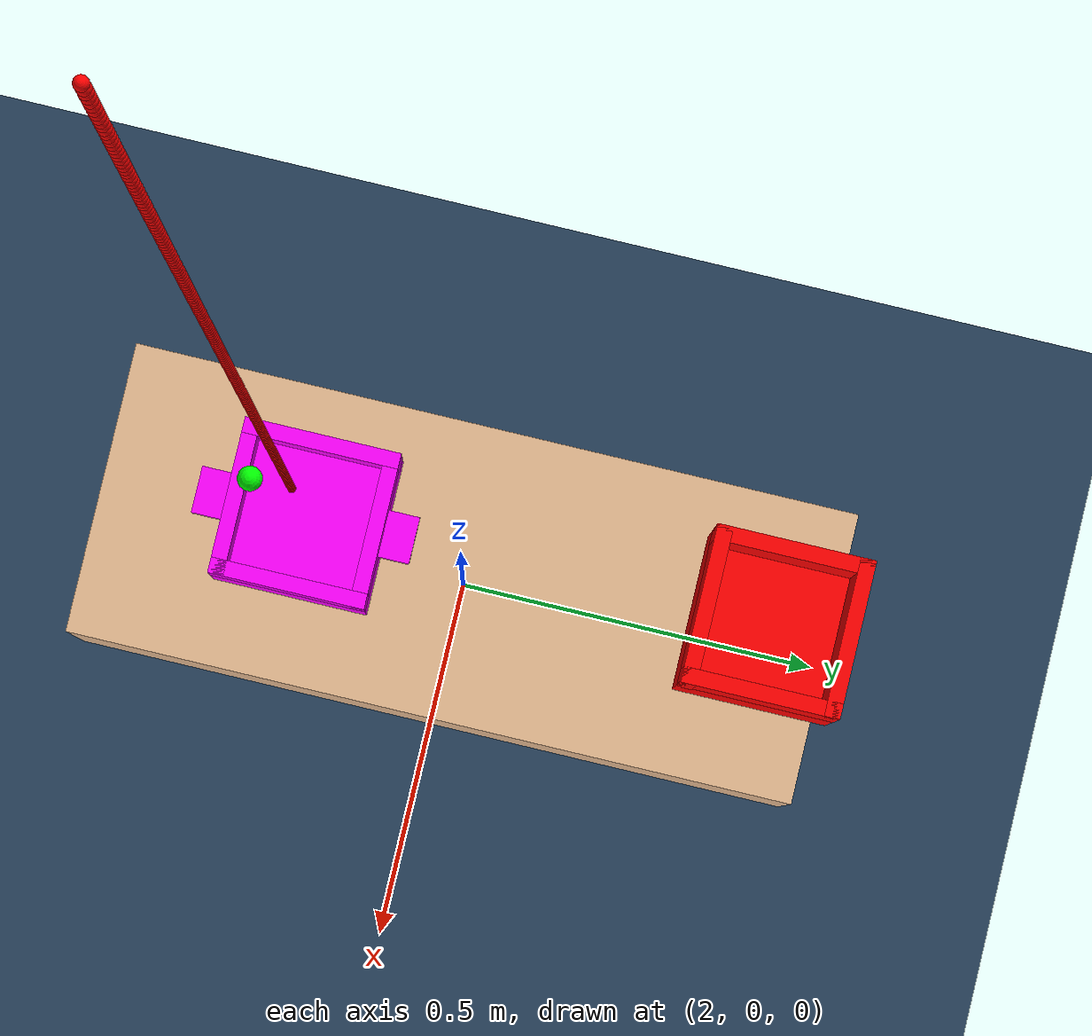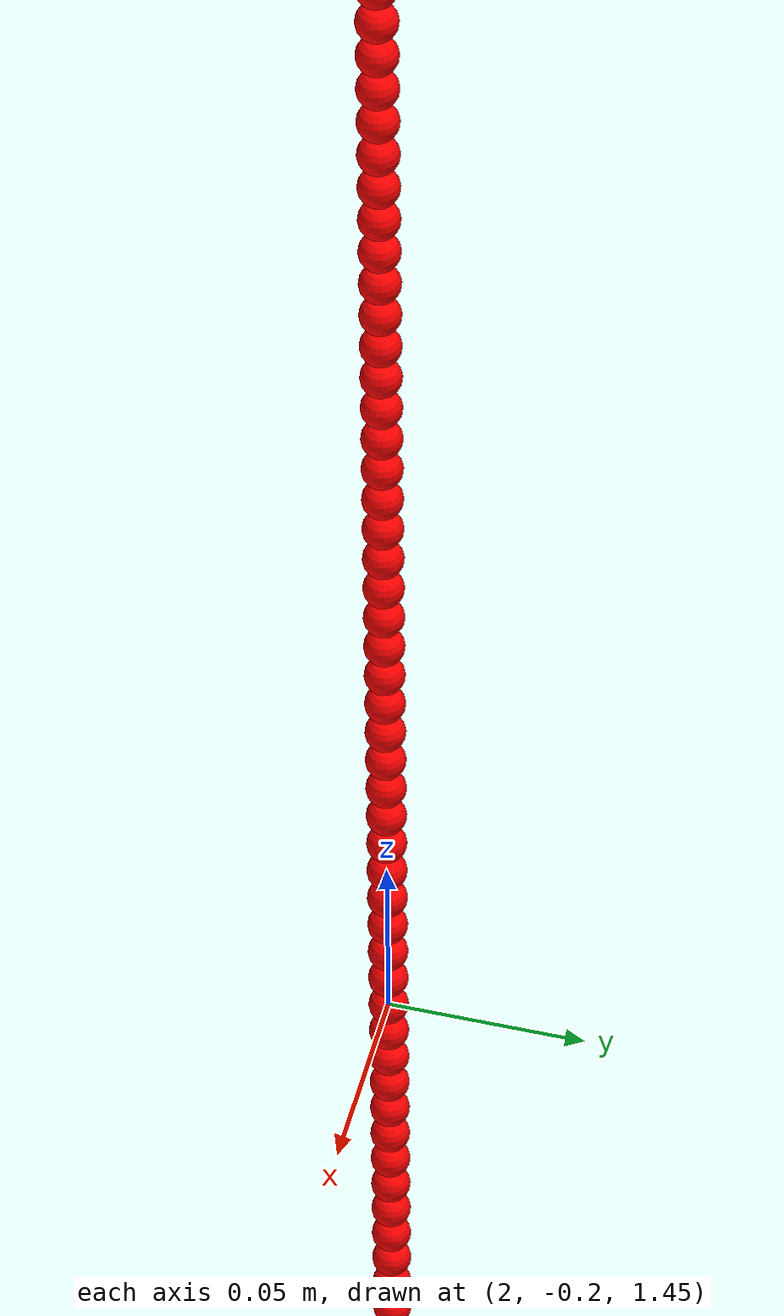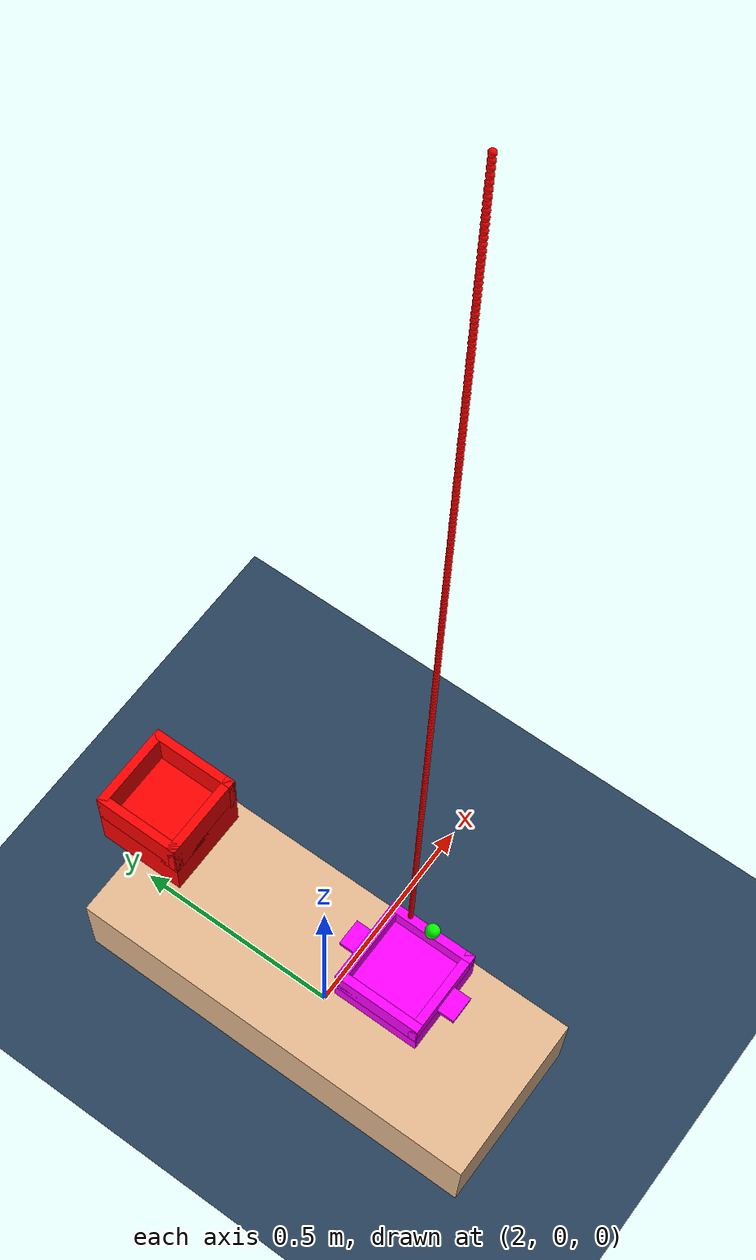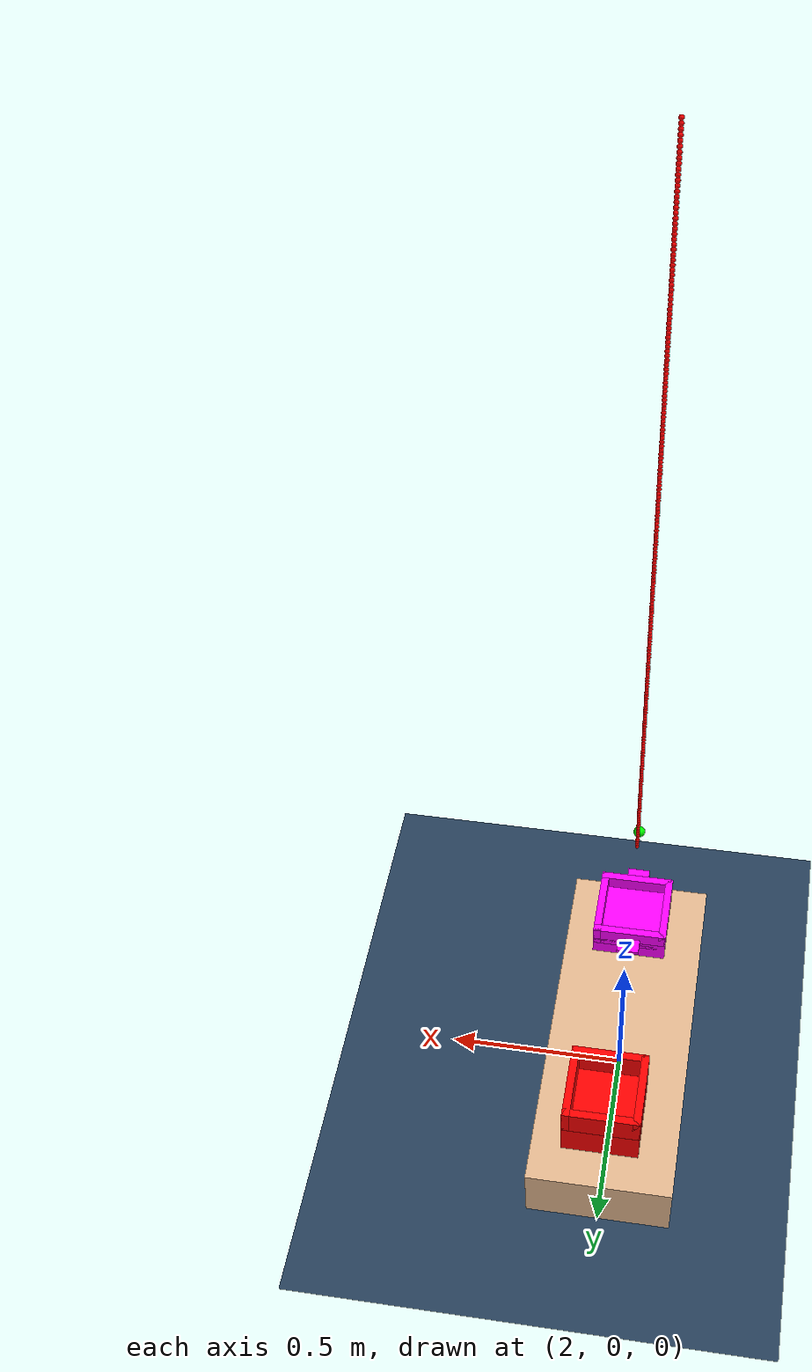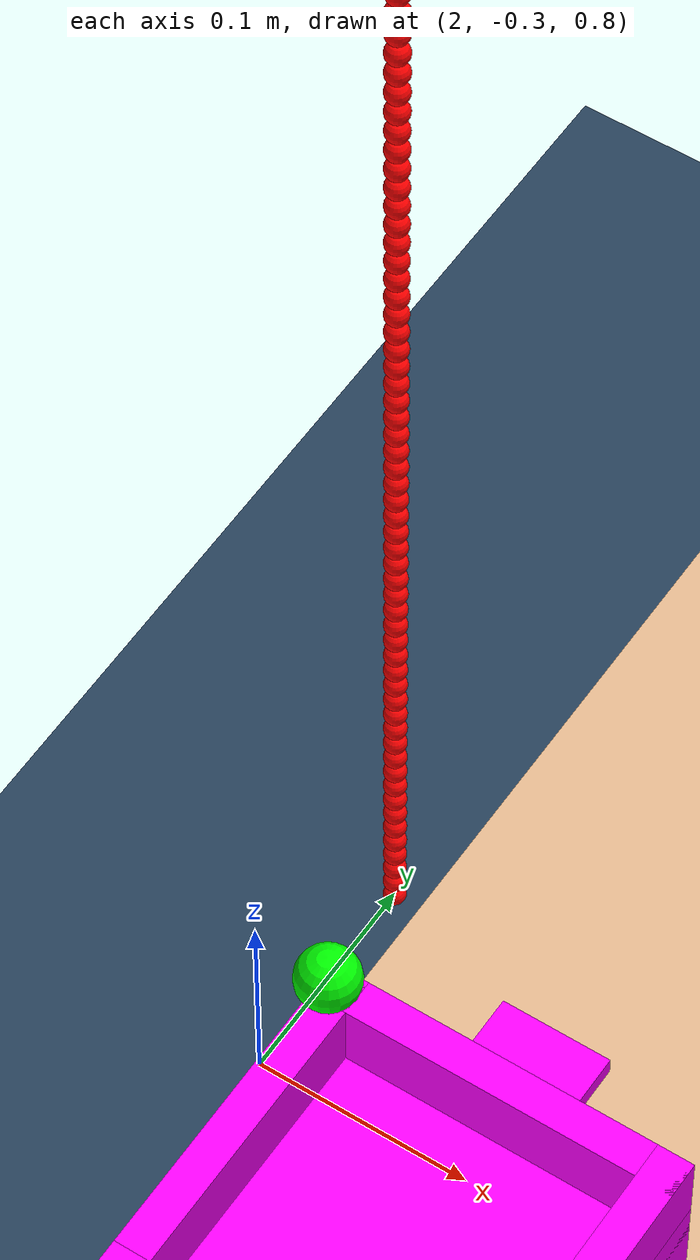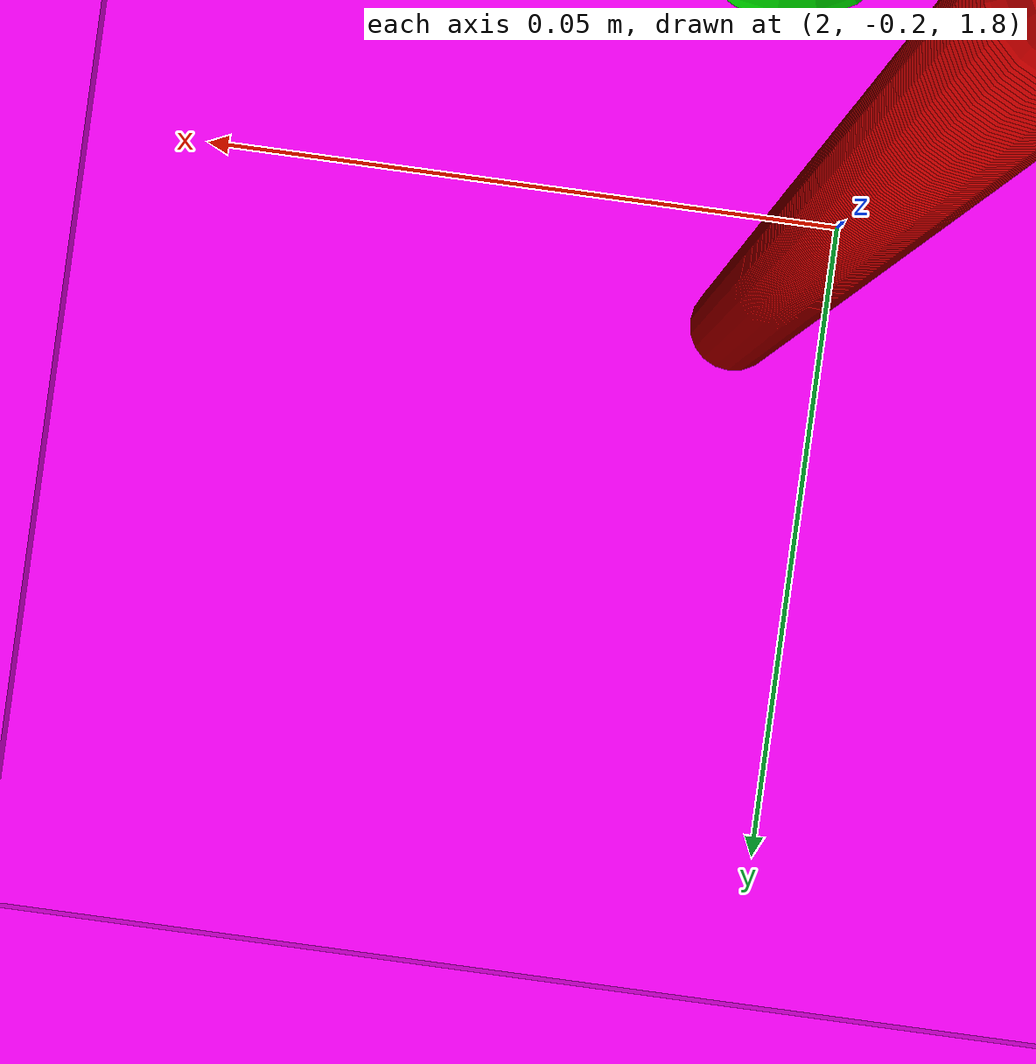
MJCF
<mujoco>
	<compiler/>
	<option timestep="0.001" integrator="RK4" solver="CG" gravity="0 0 -9.81">
		<flag sensornoise="disable" contact="enable"/>
	</option>

  <default>
        <geom condim="4" solimp="0.99 0.99 0" solref="0.01 1" friction="1 0.005 0.0001"/>
    </default>

	<asset>
		<texture name="grid" type="2d" builtin="checker" width="512" height="512" rgb1=".1 .2 .3" rgb2=".2 .3 .4" />
		<material name="grid" texture="grid" texrepeat="1 1" texuniform="true" reflectance=".2" />
	</asset>

	<worldbody>
		<geom name="floor" size="0 0 .05" type="plane" material="grid" condim="3" />
		<light diffuse="1 1 1" pos="0 0 4" dir="0 0 -1" />
		<light diffuse="1 1 1" pos="2 0 4" dir="0 0 -1" />
		<light diffuse="1 1 1" pos="1 0 4" dir="0 0 -1" />
	</worldbody>

	<worldbody>
		<body name="table" pos="2 0 0.1">
			<geom name="table_geom" type="box" size="0.2 0.5 0.1" rgba=".89 0.72 .56 1"/>
		</body>

		<body name="bowl" pos="2 0.4 0.5">
			<freejoint/>
			<geom name="bottom" type="box" size="0.1 0.1 0.05" pos="0 0 -0.04" rgba="1 0 0 1"/>

			<geom name="side1" type="box" size="0.01 0.1 0.05" pos="0.09 0 0.04" rgba="1 0 0 1"/>
			<geom name="side2" type="box" size="0.01 0.1 0.05" pos="-0.09 0 0.04" rgba="1 0 0 1"/>
			<geom name="side3" type="box" size="0.1 0.01 0.05" pos="0 0.09 0.04" rgba="1 0 0 1"/>
			<geom name="side4" type="box" size="0.1 0.01 0.05" pos="0 -0.09 0.04" rgba="1 0 0 1"/>
		</body>

        <body name="pot" pos="2 -0.2 0.5">
			<freejoint/>
			<geom name="pot_bottom" type="box" size="0.1 0.1 0.03" pos="0 0 -0.04" rgba="1 0 1 1"/>

			<geom name="pot_side1" type="box" size="0.01 0.1 0.03" pos="0.09 0 0.0" rgba="1 0 1 1"/>
			<geom name="pot_side2" type="box" size="0.01 0.1 0.03" pos="-0.09 0 0.0" rgba="1 0 1 1"/>
			<geom name="pot_side3" type="box" size="0.1 0.01 0.03" pos="0 0.09 0.0" rgba="1 0 1 1"/>
			<geom name="pot_side4" type="box" size="0.1 0.01 0.03" pos="0 -0.09 0.0" rgba="1 0 1 1"/>
			<geom name="pot_side5" type="box" size="0.03 0.02 0.005" pos="0 -0.12 0.0" rgba="1 0 1 1"/>
			<geom name="pot_side6" type="box" size="0.03 0.02 0.005" pos="0 0.12 0.0" rgba="1 0 1 1"/>
		</body>
	</worldbody>

	<worldbody>
		<body name="sync_ball0" pos="2 -0.2 0.8">
			<freejoint/><inertial pos="0.0 0.0 0.0" mass="0.0001" diaginertia="0.000000001 0.000000001 0.000000001" />
			<geom type="sphere" size="0.005" rgba="1 0 0 1"/>
		</body>
		<body name="sync_ball1" pos="2 -0.2 0.81">
			<freejoint/> <inertial pos="0.0 0.0 0.0" mass="0.0001" diaginertia="0.000000001 0.000000001 0.000000001" />
			<geom type="sphere" size="0.005" rgba="1 0 0 1"/>
		</body>
		<body name="sync_ball2" pos="2 -0.2 0.8200000000000001">
			<freejoint/> <inertial pos="0.0 0.0 0.0" mass="0.0001" diaginertia="0.000000001 0.000000001 0.000000001" />
			<geom type="sphere" size="0.005" rgba="1 0 0 1"/>
		</body>
		<body name="sync_ball3" pos="2 -0.2 0.8300000000000001">
			<freejoint/> <inertial pos="0.0 0.0 0.0" mass="0.0001" diaginertia="0.000000001 0.000000001 0.000000001" />
			<geom type="sphere" size="0.005" rgba="1 0 0 1"/>
		</body>
		<body name="sync_ball4" pos="2 -0.2 0.8400000000000001">
			<freejoint/> <inertial pos="0.0 0.0 0.0" mass="0.0001" diaginertia="0.000000001 0.000000001 0.000000001" />
			<geom type="sphere" size="0.005" rgba="1 0 0 1"/>
		</body>
		<body name="sync_ball5" pos="2 -0.2 0.8500000000000001">
			<freejoint/> <inertial pos="0.0 0.0 0.0" mass="0.0001" diaginertia="0.000000001 0.000000001 0.000000001" />
			<geom type="sphere" size="0.005" rgba="1 0 0 1"/>
		</body>
		<body name="sync_ball6" pos="2 -0.2 0.8600000000000001">
			<freejoint/> <inertial pos="0.0 0.0 0.0" mass="0.0001" diaginertia="0.000000001 0.000000001 0.000000001" />
			<geom type="sphere" size="0.005" rgba="1 0 0 1"/>
		</body>
		<body name="sync_ball7" pos="2 -0.2 0.8700000000000001">
			<freejoint/> <inertial pos="0.0 0.0 0.0" mass="0.0001" diaginertia="0.000000001 0.000000001 0.000000001" />
			<geom type="sphere" size="0.005" rgba="1 0 0 1"/>
		</body>
		<body name="sync_ball8" pos="2 -0.2 0.88">
			<freejoint/> <inertial pos="0.0 0.0 0.0" mass="0.0001" diaginertia="0.000000001 0.000000001 0.000000001" />
			<geom type="sphere" size="0.005" rgba="1 0 0 1"/>
		</body>
		<body name="sync_ball9" pos="2 -0.2 0.89">
			<freejoint/> <inertial pos="0.0 0.0 0.0" mass="0.0001" diaginertia="0.000000001 0.000000001 0.000000001" />
			<geom type="sphere" size="0.005" rgba="1 0 0 1"/>
		</body>
		<body name="sync_ball10" pos="2 -0.2 0.9">
			<freejoint/> <inertial pos="0.0 0.0 0.0" mass="0.0001" diaginertia="0.000000001 0.000000001 0.000000001" />
			<geom type="sphere" size="0.005" rgba="1 0 0 1"/>
		</body>
		<body name="sync_ball11" pos="2 -0.2 0.91">
			<freejoint/> <inertial pos="0.0 0.0 0.0" mass="0.0001" diaginertia="0.000000001 0.000000001 0.000000001" />
			<geom type="sphere" size="0.005" rgba="1 0 0 1"/>
		</body>
		<body name="sync_ball12" pos="2 -0.2 0.92">
			<freejoint/> <inertial pos="0.0 0.0 0.0" mass="0.0001" diaginertia="0.000000001 0.000000001 0.000000001" />
			<geom type="sphere" size="0.005" rgba="1 0 0 1"/>
		</body>
		<body name="sync_ball13" pos="2 -0.2 0.93">
			<freejoint/> <inertial pos="0.0 0.0 0.0" mass="0.0001" diaginertia="0.000000001 0.000000001 0.000000001" />
			<geom type="sphere" size="0.005" rgba="1 0 0 1"/>
		</body>
		<body name="sync_ball14" pos="2 -0.2 0.9400000000000001">
			<freejoint/> <inertial pos="0.0 0.0 0.0" mass="0.0001" diaginertia="0.000000001 0.000000001 0.000000001" />
			<geom type="sphere" size="0.005" rgba="1 0 0 1"/>
		</body>
		<body name="sync_ball15" pos="2 -0.2 0.9500000000000001">
			<freejoint/> <inertial pos="0.0 0.0 0.0" mass="0.0001" diaginertia="0.000000001 0.000000001 0.000000001" />
			<geom type="sphere" size="0.005" rgba="1 0 0 1"/>
		</body>
		<body name="sync_ball16" pos="2 -0.2 0.9600000000000001">
			<freejoint/> <inertial pos="0.0 0.0 0.0" mass="0.0001" diaginertia="0.000000001 0.000000001 0.000000001" />
			<geom type="sphere" size="0.005" rgba="1 0 0 1"/>
		</body>
		<body name="sync_ball17" pos="2 -0.2 0.9700000000000001">
			<freejoint/> <inertial pos="0.0 0.0 0.0" mass="0.0001" diaginertia="0.000000001 0.000000001 0.000000001" />
			<geom type="sphere" size="0.005" rgba="1 0 0 1"/>
		</body>
		<body name="sync_ball18" pos="2 -0.2 0.98">
			<freejoint/> <inertial pos="0.0 0.0 0.0" mass="0.0001" diaginertia="0.000000001 0.000000001 0.000000001" />
			<geom type="sphere" size="0.005" rgba="1 0 0 1"/>
		</body>
		<body name="sync_ball19" pos="2 -0.2 0.99">
			<freejoint/> <inertial pos="0.0 0.0 0.0" mass="0.0001" diaginertia="0.000000001 0.000000001 0.000000001" />
			<geom type="sphere" size="0.005" rgba="1 0 0 1"/>
		</body>
		<body name="sync_ball20" pos="2 -0.2 1.0">
			<freejoint/> <inertial pos="0.0 0.0 0.0" mass="0.0001" diaginertia="0.000000001 0.000000001 0.000000001" />
			<geom type="sphere" size="0.005" rgba="1 0 0 1"/>
		</body>
		<body name="sync_ball21" pos="2 -0.2 1.01">
			<freejoint/> <inertial pos="0.0 0.0 0.0" mass="0.0001" diaginertia="0.000000001 0.000000001 0.000000001" />
			<geom type="sphere" size="0.005" rgba="1 0 0 1"/>
		</body>
		<body name="sync_ball22" pos="2 -0.2 1.02">
			<freejoint/> <inertial pos="0.0 0.0 0.0" mass="0.0001" diaginertia="0.000000001 0.000000001 0.000000001" />
			<geom type="sphere" size="0.005" rgba="1 0 0 1"/>
		</body>
		<body name="sync_ball23" pos="2 -0.2 1.03">
			<freejoint/> <inertial pos="0.0 0.0 0.0" mass="0.0001" diaginertia="0.000000001 0.000000001 0.000000001" />
			<geom type="sphere" size="0.005" rgba="1 0 0 1"/>
		</body>
		<body name="sync_ball24" pos="2 -0.2 1.04">
			<freejoint/> <inertial pos="0.0 0.0 0.0" mass="0.0001" diaginertia="0.000000001 0.000000001 0.000000001" />
			<geom type="sphere" size="0.005" rgba="1 0 0 1"/>
		</body>
		<body name="sync_ball25" pos="2 -0.2 1.05">
			<freejoint/> <inertial pos="0.0 0.0 0.0" mass="0.0001" diaginertia="0.000000001 0.000000001 0.000000001" />
			<geom type="sphere" size="0.005" rgba="1 0 0 1"/>
		</body>
		<body name="sync_ball26" pos="2 -0.2 1.06">
			<freejoint/> <inertial pos="0.0 0.0 0.0" mass="0.0001" diaginertia="0.000000001 0.000000001 0.000000001" />
			<geom type="sphere" size="0.005" rgba="1 0 0 1"/>
		</body>
		<body name="sync_ball27" pos="2 -0.2 1.07">
			<freejoint/> <inertial pos="0.0 0.0 0.0" mass="0.0001" diaginertia="0.000000001 0.000000001 0.000000001" />
			<geom type="sphere" size="0.005" rgba="1 0 0 1"/>
		</body>
		<body name="sync_ball28" pos="2 -0.2 1.08">
			<freejoint/> <inertial pos="0.0 0.0 0.0" mass="0.0001" diaginertia="0.000000001 0.000000001 0.000000001" />
			<geom type="sphere" size="0.005" rgba="1 0 0 1"/>
		</body>
		<body name="sync_ball29" pos="2 -0.2 1.09">
			<freejoint/> <inertial pos="0.0 0.0 0.0" mass="0.0001" diaginertia="0.000000001 0.000000001 0.000000001" />
			<geom type="sphere" size="0.005" rgba="1 0 0 1"/>
		</body>
		<body name="sync_ball30" pos="2 -0.2 1.1">
			<freejoint/> <inertial pos="0.0 0.0 0.0" mass="0.0001" diaginertia="0.000000001 0.000000001 0.000000001" />
			<geom type="sphere" size="0.005" rgba="1 0 0 1"/>
		</body>
		<body name="sync_ball31" pos="2 -0.2 1.11">
			<freejoint/> <inertial pos="0.0 0.0 0.0" mass="0.0001" diaginertia="0.000000001 0.000000001 0.000000001" />
			<geom type="sphere" size="0.005" rgba="1 0 0 1"/>
		</body>
		<body name="sync_ball32" pos="2 -0.2 1.12">
			<freejoint/> <inertial pos="0.0 0.0 0.0" mass="0.0001" diaginertia="0.000000001 0.000000001 0.000000001" />
			<geom type="sphere" size="0.005" rgba="1 0 0 1"/>
		</body>
		<body name="sync_ball33" pos="2 -0.2 1.1300000000000001">
			<freejoint/> <inertial pos="0.0 0.0 0.0" mass="0.0001" diaginertia="0.000000001 0.000000001 0.000000001" />
			<geom type="sphere" size="0.005" rgba="1 0 0 1"/>
		</body>
		<body name="sync_ball34" pos="2 -0.2 1.1400000000000001">
			<freejoint/> <inertial pos="0.0 0.0 0.0" mass="0.0001" diaginertia="0.000000001 0.000000001 0.000000001" />
			<geom type="sphere" size="0.005" rgba="1 0 0 1"/>
		</body>
		<body name="sync_ball35" pos="2 -0.2 1.1500000000000001">
			<freejoint/> <inertial pos="0.0 0.0 0.0" mass="0.0001" diaginertia="0.000000001 0.000000001 0.000000001" />
			<geom type="sphere" size="0.005" rgba="1 0 0 1"/>
		</body>
		<body name="sync_ball36" pos="2 -0.2 1.1600000000000001">
			<freejoint/> <inertial pos="0.0 0.0 0.0" mass="0.0001" diaginertia="0.000000001 0.000000001 0.000000001" />
			<geom type="sphere" size="0.005" rgba="1 0 0 1"/>
		</body>
		<body name="sync_ball37" pos="2 -0.2 1.17">
			<freejoint/> <inertial pos="0.0 0.0 0.0" mass="0.0001" diaginertia="0.000000001 0.000000001 0.000000001" />
			<geom type="sphere" size="0.005" rgba="1 0 0 1"/>
		</body>
		<body name="sync_ball38" pos="2 -0.2 1.1800000000000002">
			<freejoint/> <inertial pos="0.0 0.0 0.0" mass="0.0001" diaginertia="0.000000001 0.000000001 0.000000001" />
			<geom type="sphere" size="0.005" rgba="1 0 0 1"/>
		</body>
		<body name="sync_ball39" pos="2 -0.2 1.19">
			<freejoint/> <inertial pos="0.0 0.0 0.0" mass="0.0001" diaginertia="0.000000001 0.000000001 0.000000001" />
			<geom type="sphere" size="0.005" rgba="1 0 0 1"/>
		</body>
		<body name="sync_ball40" pos="2 -0.2 1.2000000000000002">
			<freejoint/> <inertial pos="0.0 0.0 0.0" mass="0.0001" diaginertia="0.000000001 0.000000001 0.000000001" />
			<geom type="sphere" size="0.005" rgba="1 0 0 1"/>
		</body>
		<body name="sync_ball41" pos="2 -0.2 1.21">
			<freejoint/> <inertial pos="0.0 0.0 0.0" mass="0.0001" diaginertia="0.000000001 0.000000001 0.000000001" />
			<geom type="sphere" size="0.005" rgba="1 0 0 1"/>
		</body>
		<body name="sync_ball42" pos="2 -0.2 1.22">
			<freejoint/> <inertial pos="0.0 0.0 0.0" mass="0.0001" diaginertia="0.000000001 0.000000001 0.000000001" />
			<geom type="sphere" size="0.005" rgba="1 0 0 1"/>
		</body>
		<body name="sync_ball43" pos="2 -0.2 1.23">
			<freejoint/> <inertial pos="0.0 0.0 0.0" mass="0.0001" diaginertia="0.000000001 0.000000001 0.000000001" />
			<geom type="sphere" size="0.005" rgba="1 0 0 1"/>
		</body>
		<body name="sync_ball44" pos="2 -0.2 1.24">
			<freejoint/> <inertial pos="0.0 0.0 0.0" mass="0.0001" diaginertia="0.000000001 0.000000001 0.000000001" />
			<geom type="sphere" size="0.005" rgba="1 0 0 1"/>
		</body>
		<body name="sync_ball45" pos="2 -0.2 1.25">
			<freejoint/> <inertial pos="0.0 0.0 0.0" mass="0.0001" diaginertia="0.000000001 0.000000001 0.000000001" />
			<geom type="sphere" size="0.005" rgba="1 0 0 1"/>
		</body>
		<body name="sync_ball46" pos="2 -0.2 1.26">
			<freejoint/> <inertial pos="0.0 0.0 0.0" mass="0.0001" diaginertia="0.000000001 0.000000001 0.000000001" />
			<geom type="sphere" size="0.005" rgba="1 0 0 1"/>
		</body>
		<body name="sync_ball47" pos="2 -0.2 1.27">
			<freejoint/> <inertial pos="0.0 0.0 0.0" mass="0.0001" diaginertia="0.000000001 0.000000001 0.000000001" />
			<geom type="sphere" size="0.005" rgba="1 0 0 1"/>
		</body>
		<body name="sync_ball48" pos="2 -0.2 1.28">
			<freejoint/> <inertial pos="0.0 0.0 0.0" mass="0.0001" diaginertia="0.000000001 0.000000001 0.000000001" />
			<geom type="sphere" size="0.005" rgba="1 0 0 1"/>
		</body>
		<body name="sync_ball49" pos="2 -0.2 1.29">
			<freejoint/> <inertial pos="0.0 0.0 0.0" mass="0.0001" diaginertia="0.000000001 0.000000001 0.000000001" />
			<geom type="sphere" size="0.005" rgba="1 0 0 1"/>
		</body>
		<body name="sync_ball50" pos="2 -0.2 1.3">
			<freejoint/> <inertial pos="0.0 0.0 0.0" mass="0.0001" diaginertia="0.000000001 0.000000001 0.000000001" />
			<geom type="sphere" size="0.005" rgba="1 0 0 1"/>
		</body>
		<body name="sync_ball51" pos="2 -0.2 1.31">
			<freejoint/> <inertial pos="0.0 0.0 0.0" mass="0.0001" diaginertia="0.000000001 0.000000001 0.000000001" />
			<geom type="sphere" size="0.005" rgba="1 0 0 1"/>
		</body>
		<body name="sync_ball52" pos="2 -0.2 1.32">
			<freejoint/> <inertial pos="0.0 0.0 0.0" mass="0.0001" diaginertia="0.000000001 0.000000001 0.000000001" />
			<geom type="sphere" size="0.005" rgba="1 0 0 1"/>
		</body>
		<body name="sync_ball53" pos="2 -0.2 1.33">
			<freejoint/> <inertial pos="0.0 0.0 0.0" mass="0.0001" diaginertia="0.000000001 0.000000001 0.000000001" />
			<geom type="sphere" size="0.005" rgba="1 0 0 1"/>
		</body>
		<body name="sync_ball54" pos="2 -0.2 1.34">
			<freejoint/> <inertial pos="0.0 0.0 0.0" mass="0.0001" diaginertia="0.000000001 0.000000001 0.000000001" />
			<geom type="sphere" size="0.005" rgba="1 0 0 1"/>
		</body>
		<body name="sync_ball55" pos="2 -0.2 1.35">
			<freejoint/> <inertial pos="0.0 0.0 0.0" mass="0.0001" diaginertia="0.000000001 0.000000001 0.000000001" />
			<geom type="sphere" size="0.005" rgba="1 0 0 1"/>
		</body>
		<body name="sync_ball56" pos="2 -0.2 1.36">
			<freejoint/> <inertial pos="0.0 0.0 0.0" mass="0.0001" diaginertia="0.000000001 0.000000001 0.000000001" />
			<geom type="sphere" size="0.005" rgba="1 0 0 1"/>
		</body>
		<body name="sync_ball57" pos="2 -0.2 1.37">
			<freejoint/> <inertial pos="0.0 0.0 0.0" mass="0.0001" diaginertia="0.000000001 0.000000001 0.000000001" />
			<geom type="sphere" size="0.005" rgba="1 0 0 1"/>
		</body>
		<body name="sync_ball58" pos="2 -0.2 1.38">
			<freejoint/> <inertial pos="0.0 0.0 0.0" mass="0.0001" diaginertia="0.000000001 0.000000001 0.000000001" />
			<geom type="sphere" size="0.005" rgba="1 0 0 1"/>
		</body>
		<body name="sync_ball59" pos="2 -0.2 1.3900000000000001">
			<freejoint/> <inertial pos="0.0 0.0 0.0" mass="0.0001" diaginertia="0.000000001 0.000000001 0.000000001" />
			<geom type="sphere" size="0.005" rgba="1 0 0 1"/>
		</body>
		<body name="sync_ball60" pos="2 -0.2 1.4">
			<freejoint/> <inertial pos="0.0 0.0 0.0" mass="0.0001" diaginertia="0.000000001 0.000000001 0.000000001" />
			<geom type="sphere" size="0.005" rgba="1 0 0 1"/>
		</body>
		<body name="sync_ball61" pos="2 -0.2 1.4100000000000001">
			<freejoint/> <inertial pos="0.0 0.0 0.0" mass="0.0001" diaginertia="0.000000001 0.000000001 0.000000001" />
			<geom type="sphere" size="0.005" rgba="1 0 0 1"/>
		</body>
		<body name="sync_ball62" pos="2 -0.2 1.42">
			<freejoint/> <inertial pos="0.0 0.0 0.0" mass="0.0001" diaginertia="0.000000001 0.000000001 0.000000001" />
			<geom type="sphere" size="0.005" rgba="1 0 0 1"/>
		</body>
		<body name="sync_ball63" pos="2 -0.2 1.4300000000000002">
			<freejoint/> <inertial pos="0.0 0.0 0.0" mass="0.0001" diaginertia="0.000000001 0.000000001 0.000000001" />
			<geom type="sphere" size="0.005" rgba="1 0 0 1"/>
		</body>
		<body name="sync_ball64" pos="2 -0.2 1.44">
			<freejoint/> <inertial pos="0.0 0.0 0.0" mass="0.0001" diaginertia="0.000000001 0.000000001 0.000000001" />
			<geom type="sphere" size="0.005" rgba="1 0 0 1"/>
		</body>
		<body name="sync_ball65" pos="2 -0.2 1.4500000000000002">
			<freejoint/> <inertial pos="0.0 0.0 0.0" mass="0.0001" diaginertia="0.000000001 0.000000001 0.000000001" />
			<geom type="sphere" size="0.005" rgba="1 0 0 1"/>
		</body>
		<body name="sync_ball66" pos="2 -0.2 1.46">
			<freejoint/> <inertial pos="0.0 0.0 0.0" mass="0.0001" diaginertia="0.000000001 0.000000001 0.000000001" />
			<geom type="sphere" size="0.005" rgba="1 0 0 1"/>
		</body>
		<body name="sync_ball67" pos="2 -0.2 1.4700000000000002">
			<freejoint/> <inertial pos="0.0 0.0 0.0" mass="0.0001" diaginertia="0.000000001 0.000000001 0.000000001" />
			<geom type="sphere" size="0.005" rgba="1 0 0 1"/>
		</body>
		<body name="sync_ball68" pos="2 -0.2 1.48">
			<freejoint/> <inertial pos="0.0 0.0 0.0" mass="0.0001" diaginertia="0.000000001 0.000000001 0.000000001" />
			<geom type="sphere" size="0.005" rgba="1 0 0 1"/>
		</body>
		<body name="sync_ball69" pos="2 -0.2 1.4900000000000002">
			<freejoint/> <inertial pos="0.0 0.0 0.0" mass="0.0001" diaginertia="0.000000001 0.000000001 0.000000001" />
			<geom type="sphere" size="0.005" rgba="1 0 0 1"/>
		</body>
		<body name="sync_ball70" pos="2 -0.2 1.5">
			<freejoint/> <inertial pos="0.0 0.0 0.0" mass="0.0001" diaginertia="0.000000001 0.000000001 0.000000001" />
			<geom type="sphere" size="0.005" rgba="1 0 0 1"/>
		</body>
		<body name="sync_ball71" pos="2 -0.2 1.51">
			<freejoint/> <inertial pos="0.0 0.0 0.0" mass="0.0001" diaginertia="0.000000001 0.000000001 0.000000001" />
			<geom type="sphere" size="0.005" rgba="1 0 0 1"/>
		</body>
		<body name="sync_ball72" pos="2 -0.2 1.52">
			<freejoint/> <inertial pos="0.0 0.0 0.0" mass="0.0001" diaginertia="0.000000001 0.000000001 0.000000001" />
			<geom type="sphere" size="0.005" rgba="1 0 0 1"/>
		</body>
		<body name="sync_ball73" pos="2 -0.2 1.53">
			<freejoint/> <inertial pos="0.0 0.0 0.0" mass="0.0001" diaginertia="0.000000001 0.000000001 0.000000001" />
			<geom type="sphere" size="0.005" rgba="1 0 0 1"/>
		</body>
		<body name="sync_ball74" pos="2 -0.2 1.54">
			<freejoint/> <inertial pos="0.0 0.0 0.0" mass="0.0001" diaginertia="0.000000001 0.000000001 0.000000001" />
			<geom type="sphere" size="0.005" rgba="1 0 0 1"/>
		</body>
		<body name="sync_ball75" pos="2 -0.2 1.55">
			<freejoint/> <inertial pos="0.0 0.0 0.0" mass="0.0001" diaginertia="0.000000001 0.000000001 0.000000001" />
			<geom type="sphere" size="0.005" rgba="1 0 0 1"/>
		</body>
		<body name="sync_ball76" pos="2 -0.2 1.56">
			<freejoint/> <inertial pos="0.0 0.0 0.0" mass="0.0001" diaginertia="0.000000001 0.000000001 0.000000001" />
			<geom type="sphere" size="0.005" rgba="1 0 0 1"/>
		</body>
		<body name="sync_ball77" pos="2 -0.2 1.57">
			<freejoint/> <inertial pos="0.0 0.0 0.0" mass="0.0001" diaginertia="0.000000001 0.000000001 0.000000001" />
			<geom type="sphere" size="0.005" rgba="1 0 0 1"/>
		</body>
		<body name="sync_ball78" pos="2 -0.2 1.58">
			<freejoint/> <inertial pos="0.0 0.0 0.0" mass="0.0001" diaginertia="0.000000001 0.000000001 0.000000001" />
			<geom type="sphere" size="0.005" rgba="1 0 0 1"/>
		</body>
		<body name="sync_ball79" pos="2 -0.2 1.59">
			<freejoint/> <inertial pos="0.0 0.0 0.0" mass="0.0001" diaginertia="0.000000001 0.000000001 0.000000001" />
			<geom type="sphere" size="0.005" rgba="1 0 0 1"/>
		</body>
		<body name="sync_ball80" pos="2 -0.2 1.6">
			<freejoint/> <inertial pos="0.0 0.0 0.0" mass="0.0001" diaginertia="0.000000001 0.000000001 0.000000001" />
			<geom type="sphere" size="0.005" rgba="1 0 0 1"/>
		</body>
		<body name="sync_ball81" pos="2 -0.2 1.61">
			<freejoint/> <inertial pos="0.0 0.0 0.0" mass="0.0001" diaginertia="0.000000001 0.000000001 0.000000001" />
			<geom type="sphere" size="0.005" rgba="1 0 0 1"/>
		</body>
		<body name="sync_ball82" pos="2 -0.2 1.62">
			<freejoint/> <inertial pos="0.0 0.0 0.0" mass="0.0001" diaginertia="0.000000001 0.000000001 0.000000001" />
			<geom type="sphere" size="0.005" rgba="1 0 0 1"/>
		</body>
		<body name="sync_ball83" pos="2 -0.2 1.6300000000000001">
			<freejoint/> <inertial pos="0.0 0.0 0.0" mass="0.0001" diaginertia="0.000000001 0.000000001 0.000000001" />
			<geom type="sphere" size="0.005" rgba="1 0 0 1"/>
		</body>
		<body name="sync_ball84" pos="2 -0.2 1.6400000000000001">
			<freejoint/> <inertial pos="0.0 0.0 0.0" mass="0.0001" diaginertia="0.000000001 0.000000001 0.000000001" />
			<geom type="sphere" size="0.005" rgba="1 0 0 1"/>
		</body>
		<body name="sync_ball85" pos="2 -0.2 1.65">
			<freejoint/> <inertial pos="0.0 0.0 0.0" mass="0.0001" diaginertia="0.000000001 0.000000001 0.000000001" />
			<geom type="sphere" size="0.005" rgba="1 0 0 1"/>
		</body>
		<body name="sync_ball86" pos="2 -0.2 1.6600000000000001">
			<freejoint/> <inertial pos="0.0 0.0 0.0" mass="0.0001" diaginertia="0.000000001 0.000000001 0.000000001" />
			<geom type="sphere" size="0.005" rgba="1 0 0 1"/>
		</body>
		<body name="sync_ball87" pos="2 -0.2 1.67">
			<freejoint/> <inertial pos="0.0 0.0 0.0" mass="0.0001" diaginertia="0.000000001 0.000000001 0.000000001" />
			<geom type="sphere" size="0.005" rgba="1 0 0 1"/>
		</body>
		<body name="sync_ball88" pos="2 -0.2 1.6800000000000002">
			<freejoint/> <inertial pos="0.0 0.0 0.0" mass="0.0001" diaginertia="0.000000001 0.000000001 0.000000001" />
			<geom type="sphere" size="0.005" rgba="1 0 0 1"/>
		</body>
		<body name="sync_ball89" pos="2 -0.2 1.69">
			<freejoint/> <inertial pos="0.0 0.0 0.0" mass="0.0001" diaginertia="0.000000001 0.000000001 0.000000001" />
			<geom type="sphere" size="0.005" rgba="1 0 0 1"/>
		</body>
		<body name="sync_ball90" pos="2 -0.2 1.7000000000000002">
			<freejoint/> <inertial pos="0.0 0.0 0.0" mass="0.0001" diaginertia="0.000000001 0.000000001 0.000000001" />
			<geom type="sphere" size="0.005" rgba="1 0 0 1"/>
		</body>
		<body name="sync_ball91" pos="2 -0.2 1.71">
			<freejoint/> <inertial pos="0.0 0.0 0.0" mass="0.0001" diaginertia="0.000000001 0.000000001 0.000000001" />
			<geom type="sphere" size="0.005" rgba="1 0 0 1"/>
		</body>
		<body name="sync_ball92" pos="2 -0.2 1.7200000000000002">
			<freejoint/> <inertial pos="0.0 0.0 0.0" mass="0.0001" diaginertia="0.000000001 0.000000001 0.000000001" />
			<geom type="sphere" size="0.005" rgba="1 0 0 1"/>
		</body>
		<body name="sync_ball93" pos="2 -0.2 1.73">
			<freejoint/> <inertial pos="0.0 0.0 0.0" mass="0.0001" diaginertia="0.000000001 0.000000001 0.000000001" />
			<geom type="sphere" size="0.005" rgba="1 0 0 1"/>
		</body>
		<body name="sync_ball94" pos="2 -0.2 1.7400000000000002">
			<freejoint/> <inertial pos="0.0 0.0 0.0" mass="0.0001" diaginertia="0.000000001 0.000000001 0.000000001" />
			<geom type="sphere" size="0.005" rgba="1 0 0 1"/>
		</body>
		<body name="sync_ball95" pos="2 -0.2 1.75">
			<freejoint/> <inertial pos="0.0 0.0 0.0" mass="0.0001" diaginertia="0.000000001 0.000000001 0.000000001" />
			<geom type="sphere" size="0.005" rgba="1 0 0 1"/>
		</body>
		<body name="sync_ball96" pos="2 -0.2 1.76">
			<freejoint/> <inertial pos="0.0 0.0 0.0" mass="0.0001" diaginertia="0.000000001 0.000000001 0.000000001" />
			<geom type="sphere" size="0.005" rgba="1 0 0 1"/>
		</body>
		<body name="sync_ball97" pos="2 -0.2 1.77">
			<freejoint/> <inertial pos="0.0 0.0 0.0" mass="0.0001" diaginertia="0.000000001 0.000000001 0.000000001" />
			<geom type="sphere" size="0.005" rgba="1 0 0 1"/>
		</body>
		<body name="sync_ball98" pos="2 -0.2 1.78">
			<freejoint/> <inertial pos="0.0 0.0 0.0" mass="0.0001" diaginertia="0.000000001 0.000000001 0.000000001" />
			<geom type="sphere" size="0.005" rgba="1 0 0 1"/>
		</body>
		<body name="sync_ball99" pos="2 -0.2 1.79">
			<freejoint/> <inertial pos="0.0 0.0 0.0" mass="0.0001" diaginertia="0.000000001 0.000000001 0.000000001" />
			<geom type="sphere" size="0.005" rgba="1 0 0 1"/>
		</body>
		<body name="sync_ball100" pos="2 -0.2 1.8">
			<freejoint/> <inertial pos="0.0 0.0 0.0" mass="0.0001" diaginertia="0.000000001 0.000000001 0.000000001" />
			<geom type="sphere" size="0.005" rgba="1 0 0 1"/>
		</body>
		<body name="sync_ball101" pos="2 -0.2 1.81">
			<freejoint/> <inertial pos="0.0 0.0 0.0" mass="0.0001" diaginertia="0.000000001 0.000000001 0.000000001" />
			<geom type="sphere" size="0.005" rgba="1 0 0 1"/>
		</body>
		<body name="sync_ball102" pos="2 -0.2 1.82">
			<freejoint/> <inertial pos="0.0 0.0 0.0" mass="0.0001" diaginertia="0.000000001 0.000000001 0.000000001" />
			<geom type="sphere" size="0.005" rgba="1 0 0 1"/>
		</body>
		<body name="sync_ball103" pos="2 -0.2 1.83">
			<freejoint/> <inertial pos="0.0 0.0 0.0" mass="0.0001" diaginertia="0.000000001 0.000000001 0.000000001" />
			<geom type="sphere" size="0.005" rgba="1 0 0 1"/>
		</body>
		<body name="sync_ball104" pos="2 -0.2 1.84">
			<freejoint/> <inertial pos="0.0 0.0 0.0" mass="0.0001" diaginertia="0.000000001 0.000000001 0.000000001" />
			<geom type="sphere" size="0.005" rgba="1 0 0 1"/>
		</body>
		<body name="sync_ball105" pos="2 -0.2 1.85">
			<freejoint/> <inertial pos="0.0 0.0 0.0" mass="0.0001" diaginertia="0.000000001 0.000000001 0.000000001" />
			<geom type="sphere" size="0.005" rgba="1 0 0 1"/>
		</body>
		<body name="sync_ball106" pos="2 -0.2 1.86">
			<freejoint/> <inertial pos="0.0 0.0 0.0" mass="0.0001" diaginertia="0.000000001 0.000000001 0.000000001" />
			<geom type="sphere" size="0.005" rgba="1 0 0 1"/>
		</body>
		<body name="sync_ball107" pos="2 -0.2 1.87">
			<freejoint/> <inertial pos="0.0 0.0 0.0" mass="0.0001" diaginertia="0.000000001 0.000000001 0.000000001" />
			<geom type="sphere" size="0.005" rgba="1 0 0 1"/>
		</body>
		<body name="sync_ball108" pos="2 -0.2 1.8800000000000001">
			<freejoint/> <inertial pos="0.0 0.0 0.0" mass="0.0001" diaginertia="0.000000001 0.000000001 0.000000001" />
			<geom type="sphere" size="0.005" rgba="1 0 0 1"/>
		</body>
		<body name="sync_ball109" pos="2 -0.2 1.8900000000000001">
			<freejoint/> <inertial pos="0.0 0.0 0.0" mass="0.0001" diaginertia="0.000000001 0.000000001 0.000000001" />
			<geom type="sphere" size="0.005" rgba="1 0 0 1"/>
		</body>
		<body name="sync_ball110" pos="2 -0.2 1.9000000000000001">
			<freejoint/> <inertial pos="0.0 0.0 0.0" mass="0.0001" diaginertia="0.000000001 0.000000001 0.000000001" />
			<geom type="sphere" size="0.005" rgba="1 0 0 1"/>
		</body>
		<body name="sync_ball111" pos="2 -0.2 1.9100000000000001">
			<freejoint/> <inertial pos="0.0 0.0 0.0" mass="0.0001" diaginertia="0.000000001 0.000000001 0.000000001" />
			<geom type="sphere" size="0.005" rgba="1 0 0 1"/>
		</body>
		<body name="sync_ball112" pos="2 -0.2 1.9200000000000002">
			<freejoint/> <inertial pos="0.0 0.0 0.0" mass="0.0001" diaginertia="0.000000001 0.000000001 0.000000001" />
			<geom type="sphere" size="0.005" rgba="1 0 0 1"/>
		</body>
		<body name="sync_ball113" pos="2 -0.2 1.9300000000000002">
			<freejoint/> <inertial pos="0.0 0.0 0.0" mass="0.0001" diaginertia="0.000000001 0.000000001 0.000000001" />
			<geom type="sphere" size="0.005" rgba="1 0 0 1"/>
		</body>
		<body name="sync_ball114" pos="2 -0.2 1.9400000000000002">
			<freejoint/> <inertial pos="0.0 0.0 0.0" mass="0.0001" diaginertia="0.000000001 0.000000001 0.000000001" />
			<geom type="sphere" size="0.005" rgba="1 0 0 1"/>
		</body>
		<body name="sync_ball115" pos="2 -0.2 1.9500000000000002">
			<freejoint/> <inertial pos="0.0 0.0 0.0" mass="0.0001" diaginertia="0.000000001 0.000000001 0.000000001" />
			<geom type="sphere" size="0.005" rgba="1 0 0 1"/>
		</body>
		<body name="sync_ball116" pos="2 -0.2 1.96">
			<freejoint/> <inertial pos="0.0 0.0 0.0" mass="0.0001" diaginertia="0.000000001 0.000000001 0.000000001" />
			<geom type="sphere" size="0.005" rgba="1 0 0 1"/>
		</body>
		<body name="sync_ball117" pos="2 -0.2 1.97">
			<freejoint/> <inertial pos="0.0 0.0 0.0" mass="0.0001" diaginertia="0.000000001 0.000000001 0.000000001" />
			<geom type="sphere" size="0.005" rgba="1 0 0 1"/>
		</body>
		<body name="sync_ball118" pos="2 -0.2 1.98">
			<freejoint/> <inertial pos="0.0 0.0 0.0" mass="0.0001" diaginertia="0.000000001 0.000000001 0.000000001" />
			<geom type="sphere" size="0.005" rgba="1 0 0 1"/>
		</body>
		<body name="sync_ball119" pos="2 -0.2 1.99">
			<freejoint/> <inertial pos="0.0 0.0 0.0" mass="0.0001" diaginertia="0.000000001 0.000000001 0.000000001" />
			<geom type="sphere" size="0.005" rgba="1 0 0 1"/>
		</body>
		<body name="sync_ball120" pos="2 -0.2 2.0">
			<freejoint/> <inertial pos="0.0 0.0 0.0" mass="0.0001" diaginertia="0.000000001 0.000000001 0.000000001" />
			<geom type="sphere" size="0.005" rgba="1 0 0 1"/>
		</body>
		<body name="sync_ball121" pos="2 -0.2 2.01">
			<freejoint/> <inertial pos="0.0 0.0 0.0" mass="0.0001" diaginertia="0.000000001 0.000000001 0.000000001" />
			<geom type="sphere" size="0.005" rgba="1 0 0 1"/>
		</body>
		<body name="sync_ball122" pos="2 -0.2 2.02">
			<freejoint/> <inertial pos="0.0 0.0 0.0" mass="0.0001" diaginertia="0.000000001 0.000000001 0.000000001" />
			<geom type="sphere" size="0.005" rgba="1 0 0 1"/>
		</body>
		<body name="sync_ball123" pos="2 -0.2 2.0300000000000002">
			<freejoint/> <inertial pos="0.0 0.0 0.0" mass="0.0001" diaginertia="0.000000001 0.000000001 0.000000001" />
			<geom type="sphere" size="0.005" rgba="1 0 0 1"/>
		</body>
		<body name="sync_ball124" pos="2 -0.2 2.04">
			<freejoint/> <inertial pos="0.0 0.0 0.0" mass="0.0001" diaginertia="0.000000001 0.000000001 0.000000001" />
			<geom type="sphere" size="0.005" rgba="1 0 0 1"/>
		</body>
		<body name="sync_ball125" pos="2 -0.2 2.05">
			<freejoint/> <inertial pos="0.0 0.0 0.0" mass="0.0001" diaginertia="0.000000001 0.000000001 0.000000001" />
			<geom type="sphere" size="0.005" rgba="1 0 0 1"/>
		</body>
		<body name="sync_ball126" pos="2 -0.2 2.06">
			<freejoint/> <inertial pos="0.0 0.0 0.0" mass="0.0001" diaginertia="0.000000001 0.000000001 0.000000001" />
			<geom type="sphere" size="0.005" rgba="1 0 0 1"/>
		</body>
		<body name="sync_ball127" pos="2 -0.2 2.0700000000000003">
			<freejoint/> <inertial pos="0.0 0.0 0.0" mass="0.0001" diaginertia="0.000000001 0.000000001 0.000000001" />
			<geom type="sphere" size="0.005" rgba="1 0 0 1"/>
		</body>
		<body name="sync_ball128" pos="2 -0.2 2.08">
			<freejoint/> <inertial pos="0.0 0.0 0.0" mass="0.0001" diaginertia="0.000000001 0.000000001 0.000000001" />
			<geom type="sphere" size="0.005" rgba="1 0 0 1"/>
		</body>
		<body name="sync_ball129" pos="2 -0.2 2.09">
			<freejoint/> <inertial pos="0.0 0.0 0.0" mass="0.0001" diaginertia="0.000000001 0.000000001 0.000000001" />
			<geom type="sphere" size="0.005" rgba="1 0 0 1"/>
		</body>
		<body name="sync_ball130" pos="2 -0.2 2.1">
			<freejoint/> <inertial pos="0.0 0.0 0.0" mass="0.0001" diaginertia="0.000000001 0.000000001 0.000000001" />
			<geom type="sphere" size="0.005" rgba="1 0 0 1"/>
		</body>
		<body name="sync_ball131" pos="2 -0.2 2.1100000000000003">
			<freejoint/> <inertial pos="0.0 0.0 0.0" mass="0.0001" diaginertia="0.000000001 0.000000001 0.000000001" />
			<geom type="sphere" size="0.005" rgba="1 0 0 1"/>
		</body>
		<body name="sync_ball132" pos="2 -0.2 2.12">
			<freejoint/> <inertial pos="0.0 0.0 0.0" mass="0.0001" diaginertia="0.000000001 0.000000001 0.000000001" />
			<geom type="sphere" size="0.005" rgba="1 0 0 1"/>
		</body>
		<body name="sync_ball133" pos="2 -0.2 2.13">
			<freejoint/> <inertial pos="0.0 0.0 0.0" mass="0.0001" diaginertia="0.000000001 0.000000001 0.000000001" />
			<geom type="sphere" size="0.005" rgba="1 0 0 1"/>
		</body>
		<body name="sync_ball134" pos="2 -0.2 2.14">
			<freejoint/> <inertial pos="0.0 0.0 0.0" mass="0.0001" diaginertia="0.000000001 0.000000001 0.000000001" />
			<geom type="sphere" size="0.005" rgba="1 0 0 1"/>
		</body>
		<body name="sync_ball135" pos="2 -0.2 2.1500000000000004">
			<freejoint/> <inertial pos="0.0 0.0 0.0" mass="0.0001" diaginertia="0.000000001 0.000000001 0.000000001" />
			<geom type="sphere" size="0.005" rgba="1 0 0 1"/>
		</body>
		<body name="sync_ball136" pos="2 -0.2 2.16">
			<freejoint/> <inertial pos="0.0 0.0 0.0" mass="0.0001" diaginertia="0.000000001 0.000000001 0.000000001" />
			<geom type="sphere" size="0.005" rgba="1 0 0 1"/>
		</body>
		<body name="sync_ball137" pos="2 -0.2 2.17">
			<freejoint/> <inertial pos="0.0 0.0 0.0" mass="0.0001" diaginertia="0.000000001 0.000000001 0.000000001" />
			<geom type="sphere" size="0.005" rgba="1 0 0 1"/>
		</body>
		<body name="sync_ball138" pos="2 -0.2 2.18">
			<freejoint/> <inertial pos="0.0 0.0 0.0" mass="0.0001" diaginertia="0.000000001 0.000000001 0.000000001" />
			<geom type="sphere" size="0.005" rgba="1 0 0 1"/>
		</body>
		<body name="sync_ball139" pos="2 -0.2 2.1900000000000004">
			<freejoint/> <inertial pos="0.0 0.0 0.0" mass="0.0001" diaginertia="0.000000001 0.000000001 0.000000001" />
			<geom type="sphere" size="0.005" rgba="1 0 0 1"/>
		</body>
		<body name="sync_ball140" pos="2 -0.2 2.2">
			<freejoint/> <inertial pos="0.0 0.0 0.0" mass="0.0001" diaginertia="0.000000001 0.000000001 0.000000001" />
			<geom type="sphere" size="0.005" rgba="1 0 0 1"/>
		</body>
		<body name="sync_ball141" pos="2 -0.2 2.21">
			<freejoint/> <inertial pos="0.0 0.0 0.0" mass="0.0001" diaginertia="0.000000001 0.000000001 0.000000001" />
			<geom type="sphere" size="0.005" rgba="1 0 0 1"/>
		</body>
		<body name="sync_ball142" pos="2 -0.2 2.2199999999999998">
			<freejoint/> <inertial pos="0.0 0.0 0.0" mass="0.0001" diaginertia="0.000000001 0.000000001 0.000000001" />
			<geom type="sphere" size="0.005" rgba="1 0 0 1"/>
		</body>
		<body name="sync_ball143" pos="2 -0.2 2.23">
			<freejoint/> <inertial pos="0.0 0.0 0.0" mass="0.0001" diaginertia="0.000000001 0.000000001 0.000000001" />
			<geom type="sphere" size="0.005" rgba="1 0 0 1"/>
		</body>
		<body name="sync_ball144" pos="2 -0.2 2.24">
			<freejoint/> <inertial pos="0.0 0.0 0.0" mass="0.0001" diaginertia="0.000000001 0.000000001 0.000000001" />
			<geom type="sphere" size="0.005" rgba="1 0 0 1"/>
		</body>
		<body name="sync_ball145" pos="2 -0.2 2.25">
			<freejoint/> <inertial pos="0.0 0.0 0.0" mass="0.0001" diaginertia="0.000000001 0.000000001 0.000000001" />
			<geom type="sphere" size="0.005" rgba="1 0 0 1"/>
		</body>
		<body name="sync_ball146" pos="2 -0.2 2.26">
			<freejoint/> <inertial pos="0.0 0.0 0.0" mass="0.0001" diaginertia="0.000000001 0.000000001 0.000000001" />
			<geom type="sphere" size="0.005" rgba="1 0 0 1"/>
		</body>
		<body name="sync_ball147" pos="2 -0.2 2.27">
			<freejoint/> <inertial pos="0.0 0.0 0.0" mass="0.0001" diaginertia="0.000000001 0.000000001 0.000000001" />
			<geom type="sphere" size="0.005" rgba="1 0 0 1"/>
		</body>
		<body name="sync_ball148" pos="2 -0.2 2.2800000000000002">
			<freejoint/> <inertial pos="0.0 0.0 0.0" mass="0.0001" diaginertia="0.000000001 0.000000001 0.000000001" />
			<geom type="sphere" size="0.005" rgba="1 0 0 1"/>
		</body>
		<body name="sync_ball149" pos="2 -0.2 2.29">
			<freejoint/> <inertial pos="0.0 0.0 0.0" mass="0.0001" diaginertia="0.000000001 0.000000001 0.000000001" />
			<geom type="sphere" size="0.005" rgba="1 0 0 1"/>
		</body>
		<body name="sync_ball150" pos="2 -0.2 2.3">
			<freejoint/> <inertial pos="0.0 0.0 0.0" mass="0.0001" diaginertia="0.000000001 0.000000001 0.000000001" />
			<geom type="sphere" size="0.005" rgba="1 0 0 1"/>
		</body>
		<body name="sync_ball151" pos="2 -0.2 2.31">
			<freejoint/> <inertial pos="0.0 0.0 0.0" mass="0.0001" diaginertia="0.000000001 0.000000001 0.000000001" />
			<geom type="sphere" size="0.005" rgba="1 0 0 1"/>
		</body>
		<body name="sync_ball152" pos="2 -0.2 2.3200000000000003">
			<freejoint/> <inertial pos="0.0 0.0 0.0" mass="0.0001" diaginertia="0.000000001 0.000000001 0.000000001" />
			<geom type="sphere" size="0.005" rgba="1 0 0 1"/>
		</body>
		<body name="sync_ball153" pos="2 -0.2 2.33">
			<freejoint/> <inertial pos="0.0 0.0 0.0" mass="0.0001" diaginertia="0.000000001 0.000000001 0.000000001" />
			<geom type="sphere" size="0.005" rgba="1 0 0 1"/>
		</body>
		<body name="sync_ball154" pos="2 -0.2 2.34">
			<freejoint/> <inertial pos="0.0 0.0 0.0" mass="0.0001" diaginertia="0.000000001 0.000000001 0.000000001" />
			<geom type="sphere" size="0.005" rgba="1 0 0 1"/>
		</body>
		<body name="sync_ball155" pos="2 -0.2 2.35">
			<freejoint/> <inertial pos="0.0 0.0 0.0" mass="0.0001" diaginertia="0.000000001 0.000000001 0.000000001" />
			<geom type="sphere" size="0.005" rgba="1 0 0 1"/>
		</body>
		<body name="sync_ball156" pos="2 -0.2 2.3600000000000003">
			<freejoint/> <inertial pos="0.0 0.0 0.0" mass="0.0001" diaginertia="0.000000001 0.000000001 0.000000001" />
			<geom type="sphere" size="0.005" rgba="1 0 0 1"/>
		</body>
		<body name="sync_ball157" pos="2 -0.2 2.37">
			<freejoint/> <inertial pos="0.0 0.0 0.0" mass="0.0001" diaginertia="0.000000001 0.000000001 0.000000001" />
			<geom type="sphere" size="0.005" rgba="1 0 0 1"/>
		</body>
		<body name="sync_ball158" pos="2 -0.2 2.38">
			<freejoint/> <inertial pos="0.0 0.0 0.0" mass="0.0001" diaginertia="0.000000001 0.000000001 0.000000001" />
			<geom type="sphere" size="0.005" rgba="1 0 0 1"/>
		</body>
		<body name="sync_ball159" pos="2 -0.2 2.39">
			<freejoint/> <inertial pos="0.0 0.0 0.0" mass="0.0001" diaginertia="0.000000001 0.000000001 0.000000001" />
			<geom type="sphere" size="0.005" rgba="1 0 0 1"/>
		</body>
		<body name="sync_ball160" pos="2 -0.2 2.4000000000000004">
			<freejoint/> <inertial pos="0.0 0.0 0.0" mass="0.0001" diaginertia="0.000000001 0.000000001 0.000000001" />
			<geom type="sphere" size="0.005" rgba="1 0 0 1"/>
		</body>
		<body name="sync_ball161" pos="2 -0.2 2.41">
			<freejoint/> <inertial pos="0.0 0.0 0.0" mass="0.0001" diaginertia="0.000000001 0.000000001 0.000000001" />
			<geom type="sphere" size="0.005" rgba="1 0 0 1"/>
		</body>
		<body name="sync_ball162" pos="2 -0.2 2.42">
			<freejoint/> <inertial pos="0.0 0.0 0.0" mass="0.0001" diaginertia="0.000000001 0.000000001 0.000000001" />
			<geom type="sphere" size="0.005" rgba="1 0 0 1"/>
		</body>
		<body name="sync_ball163" pos="2 -0.2 2.43">
			<freejoint/> <inertial pos="0.0 0.0 0.0" mass="0.0001" diaginertia="0.000000001 0.000000001 0.000000001" />
			<geom type="sphere" size="0.005" rgba="1 0 0 1"/>
		</body>
		<body name="sync_ball164" pos="2 -0.2 2.4400000000000004">
			<freejoint/> <inertial pos="0.0 0.0 0.0" mass="0.0001" diaginertia="0.000000001 0.000000001 0.000000001" />
			<geom type="sphere" size="0.005" rgba="1 0 0 1"/>
		</body>
		<body name="sync_ball165" pos="2 -0.2 2.45">
			<freejoint/> <inertial pos="0.0 0.0 0.0" mass="0.0001" diaginertia="0.000000001 0.000000001 0.000000001" />
			<geom type="sphere" size="0.005" rgba="1 0 0 1"/>
		</body>
		<body name="sync_ball166" pos="2 -0.2 2.46">
			<freejoint/> <inertial pos="0.0 0.0 0.0" mass="0.0001" diaginertia="0.000000001 0.000000001 0.000000001" />
			<geom type="sphere" size="0.005" rgba="1 0 0 1"/>
		</body>
		<body name="sync_ball167" pos="2 -0.2 2.4699999999999998">
			<freejoint/> <inertial pos="0.0 0.0 0.0" mass="0.0001" diaginertia="0.000000001 0.000000001 0.000000001" />
			<geom type="sphere" size="0.005" rgba="1 0 0 1"/>
		</body>
		<body name="sync_ball168" pos="2 -0.2 2.48">
			<freejoint/> <inertial pos="0.0 0.0 0.0" mass="0.0001" diaginertia="0.000000001 0.000000001 0.000000001" />
			<geom type="sphere" size="0.005" rgba="1 0 0 1"/>
		</body>
		<body name="sync_ball169" pos="2 -0.2 2.49">
			<freejoint/> <inertial pos="0.0 0.0 0.0" mass="0.0001" diaginertia="0.000000001 0.000000001 0.000000001" />
			<geom type="sphere" size="0.005" rgba="1 0 0 1"/>
		</body>
		<body name="sync_ball170" pos="2 -0.2 2.5">
			<freejoint/> <inertial pos="0.0 0.0 0.0" mass="0.0001" diaginertia="0.000000001 0.000000001 0.000000001" />
			<geom type="sphere" size="0.005" rgba="1 0 0 1"/>
		</body>
		<body name="sync_ball171" pos="2 -0.2 2.51">
			<freejoint/> <inertial pos="0.0 0.0 0.0" mass="0.0001" diaginertia="0.000000001 0.000000001 0.000000001" />
			<geom type="sphere" size="0.005" rgba="1 0 0 1"/>
		</body>
		<body name="sync_ball172" pos="2 -0.2 2.52">
			<freejoint/> <inertial pos="0.0 0.0 0.0" mass="0.0001" diaginertia="0.000000001 0.000000001 0.000000001" />
			<geom type="sphere" size="0.005" rgba="1 0 0 1"/>
		</body>
		<body name="sync_ball173" pos="2 -0.2 2.5300000000000002">
			<freejoint/> <inertial pos="0.0 0.0 0.0" mass="0.0001" diaginertia="0.000000001 0.000000001 0.000000001" />
			<geom type="sphere" size="0.005" rgba="1 0 0 1"/>
		</body>
		<body name="sync_ball174" pos="2 -0.2 2.54">
			<freejoint/> <inertial pos="0.0 0.0 0.0" mass="0.0001" diaginertia="0.000000001 0.000000001 0.000000001" />
			<geom type="sphere" size="0.005" rgba="1 0 0 1"/>
		</body>
		<body name="sync_ball175" pos="2 -0.2 2.55">
			<freejoint/> <inertial pos="0.0 0.0 0.0" mass="0.0001" diaginertia="0.000000001 0.000000001 0.000000001" />
			<geom type="sphere" size="0.005" rgba="1 0 0 1"/>
		</body>
		<body name="sync_ball176" pos="2 -0.2 2.56">
			<freejoint/> <inertial pos="0.0 0.0 0.0" mass="0.0001" diaginertia="0.000000001 0.000000001 0.000000001" />
			<geom type="sphere" size="0.005" rgba="1 0 0 1"/>
		</body>
		<body name="sync_ball177" pos="2 -0.2 2.5700000000000003">
			<freejoint/> <inertial pos="0.0 0.0 0.0" mass="0.0001" diaginertia="0.000000001 0.000000001 0.000000001" />
			<geom type="sphere" size="0.005" rgba="1 0 0 1"/>
		</body>
		<body name="sync_ball178" pos="2 -0.2 2.58">
			<freejoint/> <inertial pos="0.0 0.0 0.0" mass="0.0001" diaginertia="0.000000001 0.000000001 0.000000001" />
			<geom type="sphere" size="0.005" rgba="1 0 0 1"/>
		</body>
		<body name="sync_ball179" pos="2 -0.2 2.59">
			<freejoint/> <inertial pos="0.0 0.0 0.0" mass="0.0001" diaginertia="0.000000001 0.000000001 0.000000001" />
			<geom type="sphere" size="0.005" rgba="1 0 0 1"/>
		</body>
		<body name="sync_ball180" pos="2 -0.2 2.6">
			<freejoint/> <inertial pos="0.0 0.0 0.0" mass="0.0001" diaginertia="0.000000001 0.000000001 0.000000001" />
			<geom type="sphere" size="0.005" rgba="1 0 0 1"/>
		</body>
		<body name="sync_ball181" pos="2 -0.2 2.6100000000000003">
			<freejoint/> <inertial pos="0.0 0.0 0.0" mass="0.0001" diaginertia="0.000000001 0.000000001 0.000000001" />
			<geom type="sphere" size="0.005" rgba="1 0 0 1"/>
		</body>
		<body name="sync_ball182" pos="2 -0.2 2.62">
			<freejoint/> <inertial pos="0.0 0.0 0.0" mass="0.0001" diaginertia="0.000000001 0.000000001 0.000000001" />
			<geom type="sphere" size="0.005" rgba="1 0 0 1"/>
		</body>
		<body name="sync_ball183" pos="2 -0.2 2.63">
			<freejoint/> <inertial pos="0.0 0.0 0.0" mass="0.0001" diaginertia="0.000000001 0.000000001 0.000000001" />
			<geom type="sphere" size="0.005" rgba="1 0 0 1"/>
		</body>
		<body name="sync_ball184" pos="2 -0.2 2.64">
			<freejoint/> <inertial pos="0.0 0.0 0.0" mass="0.0001" diaginertia="0.000000001 0.000000001 0.000000001" />
			<geom type="sphere" size="0.005" rgba="1 0 0 1"/>
		</body>
		<body name="sync_ball185" pos="2 -0.2 2.6500000000000004">
			<freejoint/> <inertial pos="0.0 0.0 0.0" mass="0.0001" diaginertia="0.000000001 0.000000001 0.000000001" />
			<geom type="sphere" size="0.005" rgba="1 0 0 1"/>
		</body>
		<body name="sync_ball186" pos="2 -0.2 2.66">
			<freejoint/> <inertial pos="0.0 0.0 0.0" mass="0.0001" diaginertia="0.000000001 0.000000001 0.000000001" />
			<geom type="sphere" size="0.005" rgba="1 0 0 1"/>
		</body>
		<body name="sync_ball187" pos="2 -0.2 2.67">
			<freejoint/> <inertial pos="0.0 0.0 0.0" mass="0.0001" diaginertia="0.000000001 0.000000001 0.000000001" />
			<geom type="sphere" size="0.005" rgba="1 0 0 1"/>
		</body>
		<body name="sync_ball188" pos="2 -0.2 2.68">
			<freejoint/> <inertial pos="0.0 0.0 0.0" mass="0.0001" diaginertia="0.000000001 0.000000001 0.000000001" />
			<geom type="sphere" size="0.005" rgba="1 0 0 1"/>
		</body>
		<body name="sync_ball189" pos="2 -0.2 2.6900000000000004">
			<freejoint/> <inertial pos="0.0 0.0 0.0" mass="0.0001" diaginertia="0.000000001 0.000000001 0.000000001" />
			<geom type="sphere" size="0.005" rgba="1 0 0 1"/>
		</body>
		<body name="sync_ball190" pos="2 -0.2 2.7">
			<freejoint/> <inertial pos="0.0 0.0 0.0" mass="0.0001" diaginertia="0.000000001 0.000000001 0.000000001" />
			<geom type="sphere" size="0.005" rgba="1 0 0 1"/>
		</body>
		<body name="sync_ball191" pos="2 -0.2 2.71">
			<freejoint/> <inertial pos="0.0 0.0 0.0" mass="0.0001" diaginertia="0.000000001 0.000000001 0.000000001" />
			<geom type="sphere" size="0.005" rgba="1 0 0 1"/>
		</body>
		<body name="sync_ball192" pos="2 -0.2 2.7199999999999998">
			<freejoint/> <inertial pos="0.0 0.0 0.0" mass="0.0001" diaginertia="0.000000001 0.000000001 0.000000001" />
			<geom type="sphere" size="0.005" rgba="1 0 0 1"/>
		</body>
		<body name="sync_ball193" pos="2 -0.2 2.73">
			<freejoint/> <inertial pos="0.0 0.0 0.0" mass="0.0001" diaginertia="0.000000001 0.000000001 0.000000001" />
			<geom type="sphere" size="0.005" rgba="1 0 0 1"/>
		</body>
		<body name="sync_ball194" pos="2 -0.2 2.74">
			<freejoint/> <inertial pos="0.0 0.0 0.0" mass="0.0001" diaginertia="0.000000001 0.000000001 0.000000001" />
			<geom type="sphere" size="0.005" rgba="1 0 0 1"/>
		</body>
		<body name="sync_ball195" pos="2 -0.2 2.75">
			<freejoint/> <inertial pos="0.0 0.0 0.0" mass="0.0001" diaginertia="0.000000001 0.000000001 0.000000001" />
			<geom type="sphere" size="0.005" rgba="1 0 0 1"/>
		</body>
		<body name="sync_ball196" pos="2 -0.2 2.76">
			<freejoint/> <inertial pos="0.0 0.0 0.0" mass="0.0001" diaginertia="0.000000001 0.000000001 0.000000001" />
			<geom type="sphere" size="0.005" rgba="1 0 0 1"/>
		</body>
		<body name="sync_ball197" pos="2 -0.2 2.77">
			<freejoint/> <inertial pos="0.0 0.0 0.0" mass="0.0001" diaginertia="0.000000001 0.000000001 0.000000001" />
			<geom type="sphere" size="0.005" rgba="1 0 0 1"/>
		</body>
		<body name="sync_ball198" pos="2 -0.2 2.7800000000000002">
			<freejoint/> <inertial pos="0.0 0.0 0.0" mass="0.0001" diaginertia="0.000000001 0.000000001 0.000000001" />
			<geom type="sphere" size="0.005" rgba="1 0 0 1"/>
		</body>
		<body name="sync_ball199" pos="2 -0.2 2.79">
			<freejoint/> <inertial pos="0.0 0.0 0.0" mass="0.0001" diaginertia="0.000000001 0.000000001 0.000000001" />
			<geom type="sphere" size="0.005" rgba="1 0 0 1"/>
		</body>
        <body name="big_ball" pos="2 -0.25 0.8">
			<freejoint/> <inertial pos="0.0 0.0 0.0" mass="0.0001" diaginertia="0.000000001 0.000000001 0.000000001" />
			<geom type="sphere" size="0.015" rgba="0 1 0 1"/>
		</body>
	</worldbody>

</mujoco>
